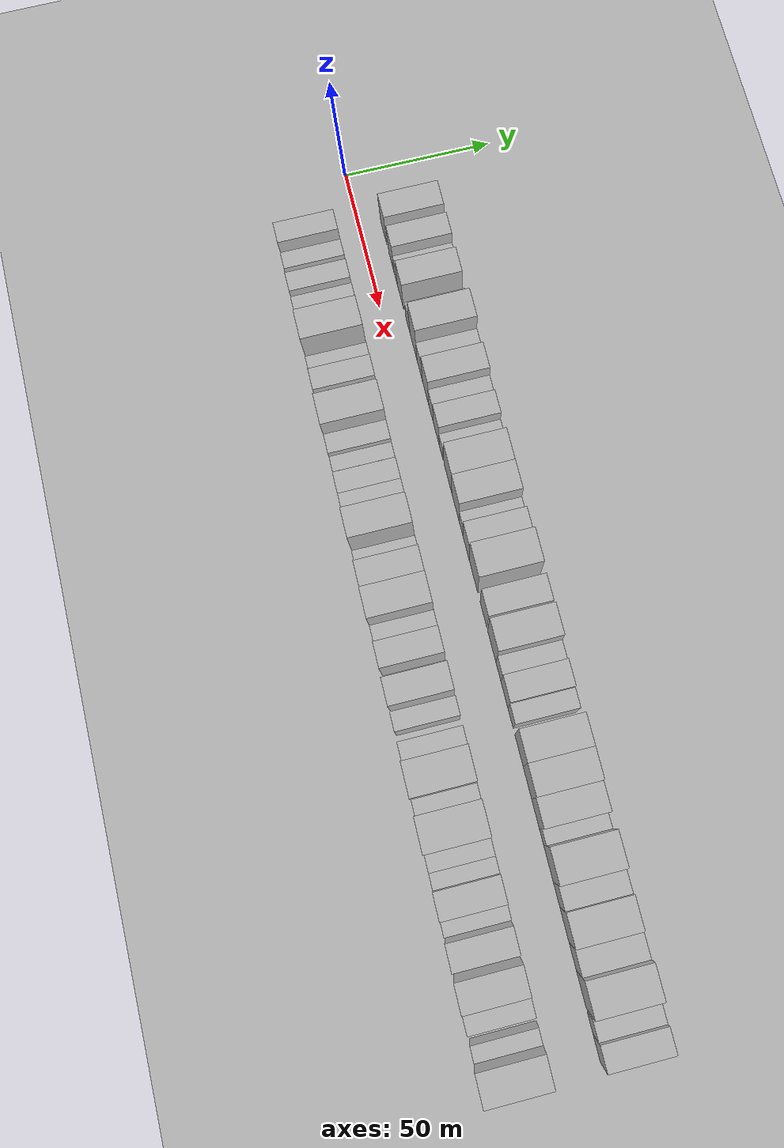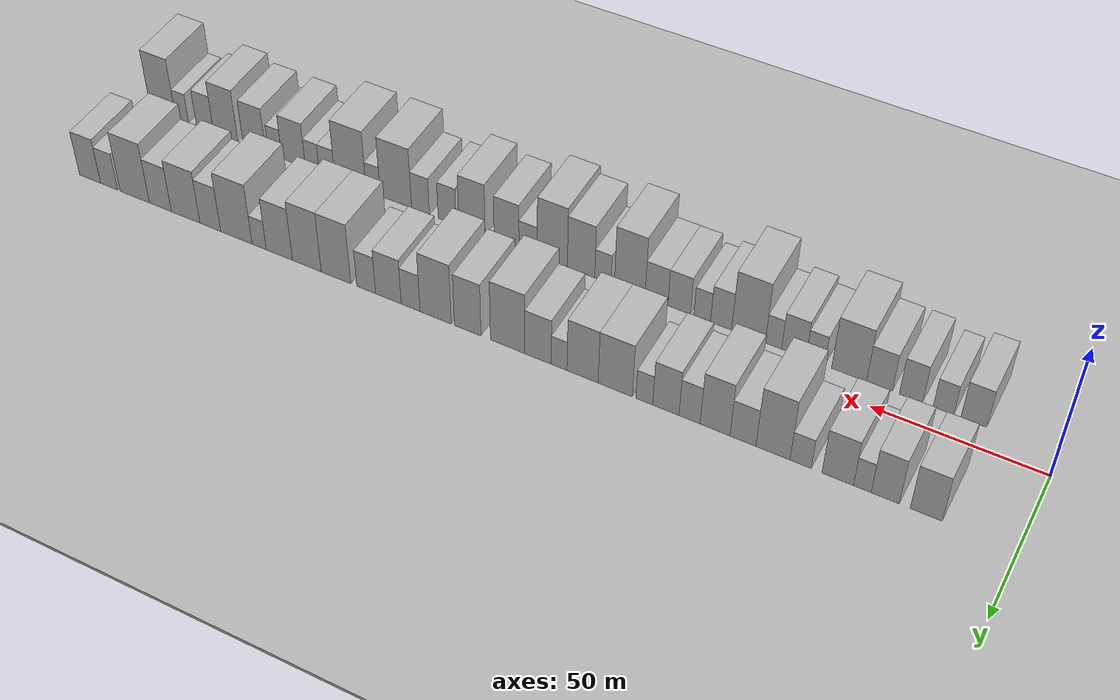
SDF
<?xml version="1.0" encoding="utf-8"?>

<sdf version="1.6">

   <world name="default">

      <gui fullscreen="0">

         <camera name="user_camera">

            <pose>-15 0 4.57585 0 0 0</pose>

            <view_controller>orbit</view_controller>

         </camera>

      </gui>

      <scene>

         <sky>

           <clouds>

             <speed>12</speed>

           </clouds>

         </sky>

         <ambient>0.4 0.4 0.4 1</ambient>

         <background>0.7 0.7 0.7 1</background>

         <shadows>1</shadows>

      </scene>

      <gravity>0 0 -9.8066</gravity>

      <magnetic_field>6e-06 2.3e-05 -4.2e-05</magnetic_field>

      <physics default="0" name="default_physics" type="ode">

         <ode>

            <solver>

               <type>quick</type>

               <iters>10</iters>

               <sor>1.0</sor>

               <use_dynamic_moi_rescaling>0</use_dynamic_moi_rescaling>

            </solver>

            <constraints>

               <cfm>0</cfm>

               <erp>0.2</erp>

               <contact_max_correcting_vel>100</contact_max_correcting_vel>

               <contact_surface_layer>0.001</contact_surface_layer>

            </constraints>

         </ode>

         <max_step_size>0.004</max_step_size>

         <real_time_factor>1</real_time_factor>

         <real_time_update_rate>250</real_time_update_rate>

      </physics>

      <light name="sun" type="directional">

         <cast_shadows>1</cast_shadows>

         <pose>0 0 10 0 0 0</pose>

         <diffuse>0.8 0.8 0.8 1</diffuse>

         <specular>0.2 0.2 0.2 1</specular>

         <attenuation>

            <range>1000</range>

            <constant>0.9</constant>

            <linear>0.01</linear>

            <quadratic>0.001</quadratic>

         </attenuation>

         <direction>-0.5 0.1 -0.9</direction>

      </light>

      <include>

         <name>ground_plane_1</name>

         <uri>model://HANNAS_ground_plane</uri>

         <pose>0 0 0  0 0 0</pose>

      </include>

      <include>

         <name>ground_plane_2</name>

         <uri>model://HANNAS_ground_plane</uri>

         <pose>100 0 0  0 0 0</pose>

      </include>

      <model name="building_1">

         <static>1</static>

         <pose frame="">24.3288 17.5000 0 0.000000 0.000000 1.570796</pose>

         <link name="link">

            <pose frame="">0 0 9.00 0 0 0</pose>

            <collision name="collision">

               <geometry>

                  <box>

                     <size>20.0000 8.6577 18.0000</size>

                  </box>

               </geometry>

               <max_contacts>10</max_contacts>

               <surface>

                  <contact>

                     <ode/>

                  </contact>

                  <bounce/>

                  <friction>

                     <torsional>

                        <ode/>

                     </torsional>

                     <ode/>

                  </friction>

               </surface>

            </collision>

            <visual name="visual">

               <cast_shadows>0</cast_shadows>

               <geometry>

                  <box>

                     <size>20.0000 8.6577 18.0000</size>

                  </box>

               </geometry>

               <material>

                  <script>

                     <uri>model://HANNAS_wall/materials/scripts</uri>

                     <uri>model://HANNAS_wall/materials/textures</uri>

                     <name>vrc/HANNAS_wall</name>

                  </script>

               </material>

            </visual>

            <self_collide>0</self_collide>

            <enable_wind>0</enable_wind>

            <kinematic>0</kinematic>

         </link>

      </model>

      <model name="building_2">

         <static>1</static>

         <pose frame="">35.4990 17.5000 0 0.000000 0.000000 1.570796</pose>

         <link name="link">

            <pose frame="">0 0 9.00 0 0 0</pose>

            <collision name="collision">

               <geometry>

                  <box>

                     <size>20.0000 7.6827 18.0000</size>

                  </box>

               </geometry>

               <max_contacts>10</max_contacts>

               <surface>

                  <contact>

                     <ode/>

                  </contact>

                  <bounce/>

                  <friction>

                     <torsional>

                        <ode/>

                     </torsional>

                     <ode/>

                  </friction>

               </surface>

            </collision>

            <visual name="visual">

               <cast_shadows>0</cast_shadows>

               <geometry>

                  <box>

                     <size>20.0000 7.6827 18.0000</size>

                  </box>

               </geometry>

               <material>

                  <script>

                     <uri>model://HANNAS_wall/materials/scripts</uri>

                     <uri>model://HANNAS_wall/materials/textures</uri>

                     <name>vrc/HANNAS_wall</name>

                  </script>

               </material>

            </visual>

            <self_collide>0</self_collide>

            <enable_wind>0</enable_wind>

            <kinematic>0</kinematic>

         </link>

      </model>

      <model name="building_3">

         <static>1</static>

         <pose frame="">41.7820 17.5000 0 0.000000 0.000000 1.570796</pose>

         <link name="link">

            <pose frame="">0 0 6.00 0 0 0</pose>

            <collision name="collision">

               <geometry>

                  <box>

                     <size>20.0000 4.8833 12.0000</size>

                  </box>

               </geometry>

               <max_contacts>10</max_contacts>

               <surface>

                  <contact>

                     <ode/>

                  </contact>

                  <bounce/>

                  <friction>

                     <torsional>

                        <ode/>

                     </torsional>

                     <ode/>

                  </friction>

               </surface>

            </collision>

            <visual name="visual">

               <cast_shadows>0</cast_shadows>

               <geometry>

                  <box>

                     <size>20.0000 4.8833 12.0000</size>

                  </box>

               </geometry>

               <material>

                  <script>

                     <uri>model://HANNAS_wall/materials/scripts</uri>

                     <uri>model://HANNAS_wall/materials/textures</uri>

                     <name>vrc/HANNAS_wall</name>

                  </script>

               </material>

            </visual>

            <self_collide>0</self_collide>

            <enable_wind>0</enable_wind>

            <kinematic>0</kinematic>

         </link>

      </model>

      <model name="building_4">

         <static>1</static>

         <pose frame="">48.6134 17.5000 0 0.000000 0.000000 1.570796</pose>

         <link name="link">

            <pose frame="">0 0 9.00 0 0 0</pose>

            <collision name="collision">

               <geometry>

                  <box>

                     <size>20.0000 8.7796 18.0000</size>

                  </box>

               </geometry>

               <max_contacts>10</max_contacts>

               <surface>

                  <contact>

                     <ode/>

                  </contact>

                  <bounce/>

                  <friction>

                     <torsional>

                        <ode/>

                     </torsional>

                     <ode/>

                  </friction>

               </surface>

            </collision>

            <visual name="visual">

               <cast_shadows>0</cast_shadows>

               <geometry>

                  <box>

                     <size>20.0000 8.7796 18.0000</size>

                  </box>

               </geometry>

               <material>

                  <script>

                     <uri>model://HANNAS_wall/materials/scripts</uri>

                     <uri>model://HANNAS_wall/materials/textures</uri>

                     <name>vrc/HANNAS_wall</name>

                  </script>

               </material>

            </visual>

            <self_collide>0</self_collide>

            <enable_wind>0</enable_wind>

            <kinematic>0</kinematic>

         </link>

      </model>

      <model name="building_5">

         <static>1</static>

         <pose frame="">59.0030 17.5000 0 0.000000 0.000000 1.570796</pose>

         <link name="link">

            <pose frame="">0 0 6.00 0 0 0</pose>

            <collision name="collision">

               <geometry>

                  <box>

                     <size>20.0000 5.9996 12.0000</size>

                  </box>

               </geometry>

               <max_contacts>10</max_contacts>

               <surface>

                  <contact>

                     <ode/>

                  </contact>

                  <bounce/>

                  <friction>

                     <torsional>

                        <ode/>

                     </torsional>

                     <ode/>

                  </friction>

               </surface>

            </collision>

            <visual name="visual">

               <cast_shadows>0</cast_shadows>

               <geometry>

                  <box>

                     <size>20.0000 5.9996 12.0000</size>

                  </box>

               </geometry>

               <material>

                  <script>

                     <uri>model://HANNAS_wall/materials/scripts</uri>

                     <uri>model://HANNAS_wall/materials/textures</uri>

                     <name>vrc/HANNAS_wall</name>

                  </script>

               </material>

            </visual>

            <self_collide>0</self_collide>

            <enable_wind>0</enable_wind>

            <kinematic>0</kinematic>

         </link>

      </model>

      <model name="building_6">

         <static>1</static>

         <pose frame="">66.8728 17.5000 0 0.000000 0.000000 1.570796</pose>

         <link name="link">

            <pose frame="">0 0 12.00 0 0 0</pose>

            <collision name="collision">

               <geometry>

                  <box>

                     <size>20.0000 9.7398 24.0000</size>

                  </box>

               </geometry>

               <max_contacts>10</max_contacts>

               <surface>

                  <contact>

                     <ode/>

                  </contact>

                  <bounce/>

                  <friction>

                     <torsional>

                        <ode/>

                     </torsional>

                     <ode/>

                  </friction>

               </surface>

            </collision>

            <visual name="visual">

               <cast_shadows>0</cast_shadows>

               <geometry>

                  <box>

                     <size>20.0000 9.7398 24.0000</size>

                  </box>

               </geometry>

               <material>

                  <script>

                     <uri>model://HANNAS_wall/materials/scripts</uri>

                     <uri>model://HANNAS_wall/materials/textures</uri>

                     <name>vrc/HANNAS_wall</name>

                  </script>

               </material>

            </visual>

            <self_collide>0</self_collide>

            <enable_wind>0</enable_wind>

            <kinematic>0</kinematic>

         </link>

      </model>

      <model name="building_7">

         <static>1</static>

         <pose frame="">75.4735 17.5000 0 0.000000 0.000000 1.570796</pose>

         <link name="link">

            <pose frame="">0 0 7.50 0 0 0</pose>

            <collision name="collision">

               <geometry>

                  <box>

                     <size>20.0000 7.4617 15.0000</size>

                  </box>

               </geometry>

               <max_contacts>10</max_contacts>

               <surface>

                  <contact>

                     <ode/>

                  </contact>

                  <bounce/>

                  <friction>

                     <torsional>

                        <ode/>

                     </torsional>

                     <ode/>

                  </friction>

               </surface>

            </collision>

            <visual name="visual">

               <cast_shadows>0</cast_shadows>

               <geometry>

                  <box>

                     <size>20.0000 7.4617 15.0000</size>

                  </box>

               </geometry>

               <material>

                  <script>

                     <uri>model://HANNAS_wall/materials/scripts</uri>

                     <uri>model://HANNAS_wall/materials/textures</uri>

                     <name>vrc/HANNAS_wall</name>

                  </script>

               </material>

            </visual>

            <self_collide>0</self_collide>

            <enable_wind>0</enable_wind>

            <kinematic>0</kinematic>

         </link>

      </model>

      <model name="building_8">

         <static>1</static>

         <pose frame="">83.5701 17.5000 0 0.000000 0.000000 1.570796</pose>

         <link name="link">

            <pose frame="">0 0 10.50 0 0 0</pose>

            <collision name="collision">

               <geometry>

                  <box>

                     <size>20.0000 8.7315 21.0000</size>

                  </box>

               </geometry>

               <max_contacts>10</max_contacts>

               <surface>

                  <contact>

                     <ode/>

                  </contact>

                  <bounce/>

                  <friction>

                     <torsional>

                        <ode/>

                     </torsional>

                     <ode/>

                  </friction>

               </surface>

            </collision>

            <visual name="visual">

               <cast_shadows>0</cast_shadows>

               <geometry>

                  <box>

                     <size>20.0000 8.7315 21.0000</size>

                  </box>

               </geometry>

               <material>

                  <script>

                     <uri>model://HANNAS_wall/materials/scripts</uri>

                     <uri>model://HANNAS_wall/materials/textures</uri>

                     <name>vrc/HANNAS_wall</name>

                  </script>

               </material>

            </visual>

            <self_collide>0</self_collide>

            <enable_wind>0</enable_wind>

            <kinematic>0</kinematic>

         </link>

      </model>

      <model name="building_9">

         <static>1</static>

         <pose frame="">91.0407 17.5000 0 0.000000 0.000000 1.570796</pose>

         <link name="link">

            <pose frame="">0 0 7.50 0 0 0</pose>

            <collision name="collision">

               <geometry>

                  <box>

                     <size>20.0000 6.2097 15.0000</size>

                  </box>

               </geometry>

               <max_contacts>10</max_contacts>

               <surface>

                  <contact>

                     <ode/>

                  </contact>

                  <bounce/>

                  <friction>

                     <torsional>

                        <ode/>

                     </torsional>

                     <ode/>

                  </friction>

               </surface>

            </collision>

            <visual name="visual">

               <cast_shadows>0</cast_shadows>

               <geometry>

                  <box>

                     <size>20.0000 6.2097 15.0000</size>

                  </box>

               </geometry>

               <material>

                  <script>

                     <uri>model://HANNAS_wall/materials/scripts</uri>

                     <uri>model://HANNAS_wall/materials/textures</uri>

                     <name>vrc/HANNAS_wall</name>

                  </script>

               </material>

            </visual>

            <self_collide>0</self_collide>

            <enable_wind>0</enable_wind>

            <kinematic>0</kinematic>

         </link>

      </model>

      <model name="building_10">

         <static>1</static>

         <pose frame="">98.0474 17.5000 0 0.000000 0.000000 1.570796</pose>

         <link name="link">

            <pose frame="">0 0 9.00 0 0 0</pose>

            <collision name="collision">

               <geometry>

                  <box>

                     <size>20.0000 7.8037 18.0000</size>

                  </box>

               </geometry>

               <max_contacts>10</max_contacts>

               <surface>

                  <contact>

                     <ode/>

                  </contact>

                  <bounce/>

                  <friction>

                     <torsional>

                        <ode/>

                     </torsional>

                     <ode/>

                  </friction>

               </surface>

            </collision>

            <visual name="visual">

               <cast_shadows>0</cast_shadows>

               <geometry>

                  <box>

                     <size>20.0000 7.8037 18.0000</size>

                  </box>

               </geometry>

               <material>

                  <script>

                     <uri>model://HANNAS_wall/materials/scripts</uri>

                     <uri>model://HANNAS_wall/materials/textures</uri>

                     <name>vrc/HANNAS_wall</name>

                  </script>

               </material>

            </visual>

            <self_collide>0</self_collide>

            <enable_wind>0</enable_wind>

            <kinematic>0</kinematic>

         </link>

      </model>

      <model name="building_11">

         <static>1</static>

         <pose frame="">104.4831 17.5000 0 0.000000 0.000000 1.570796</pose>

         <link name="link">

            <pose frame="">0 0 6.00 0 0 0</pose>

            <collision name="collision">

               <geometry>

                  <box>

                     <size>20.0000 5.0678 12.0000</size>

                  </box>

               </geometry>

               <max_contacts>10</max_contacts>

               <surface>

                  <contact>

                     <ode/>

                  </contact>

                  <bounce/>

                  <friction>

                     <torsional>

                        <ode/>

                     </torsional>

                     <ode/>

                  </friction>

               </surface>

            </collision>

            <visual name="visual">

               <cast_shadows>0</cast_shadows>

               <geometry>

                  <box>

                     <size>20.0000 5.0678 12.0000</size>

                  </box>

               </geometry>

               <material>

                  <script>

                     <uri>model://HANNAS_wall/materials/scripts</uri>

                     <uri>model://HANNAS_wall/materials/textures</uri>

                     <name>vrc/HANNAS_wall</name>

                  </script>

               </material>

            </visual>

            <self_collide>0</self_collide>

            <enable_wind>0</enable_wind>

            <kinematic>0</kinematic>

         </link>

      </model>

      <model name="building_12">

         <static>1</static>

         <pose frame="">113.2187 17.5000 0 0.000000 0.000000 1.570796</pose>

         <link name="link">

            <pose frame="">0 0 10.50 0 0 0</pose>

            <collision name="collision">

               <geometry>

                  <box>

                     <size>20.0000 10.4034 21.0000</size>

                  </box>

               </geometry>

               <max_contacts>10</max_contacts>

               <surface>

                  <contact>

                     <ode/>

                  </contact>

                  <bounce/>

                  <friction>

                     <torsional>

                        <ode/>

                     </torsional>

                     <ode/>

                  </friction>

               </surface>

            </collision>

            <visual name="visual">

               <cast_shadows>0</cast_shadows>

               <geometry>

                  <box>

                     <size>20.0000 10.4034 21.0000</size>

                  </box>

               </geometry>

               <material>

                  <script>

                     <uri>model://HANNAS_wall/materials/scripts</uri>

                     <uri>model://HANNAS_wall/materials/textures</uri>

                     <name>vrc/HANNAS_wall</name>

                  </script>

               </material>

            </visual>

            <self_collide>0</self_collide>

            <enable_wind>0</enable_wind>

            <kinematic>0</kinematic>

         </link>

      </model>

      <model name="building_13">

         <static>1</static>

         <pose frame="">123.2028 17.5000 0 0.000000 0.000000 1.570796</pose>

         <link name="link">

            <pose frame="">0 0 10.50 0 0 0</pose>

            <collision name="collision">

               <geometry>

                  <box>

                     <size>20.0000 9.5647 21.0000</size>

                  </box>

               </geometry>

               <max_contacts>10</max_contacts>

               <surface>

                  <contact>

                     <ode/>

                  </contact>

                  <bounce/>

                  <friction>

                     <torsional>

                        <ode/>

                     </torsional>

                     <ode/>

                  </friction>

               </surface>

            </collision>

            <visual name="visual">

               <cast_shadows>0</cast_shadows>

               <geometry>

                  <box>

                     <size>20.0000 9.5647 21.0000</size>

                  </box>

               </geometry>

               <material>

                  <script>

                     <uri>model://HANNAS_wall/materials/scripts</uri>

                     <uri>model://HANNAS_wall/materials/textures</uri>

                     <name>vrc/HANNAS_wall</name>

                  </script>

               </material>

            </visual>

            <self_collide>0</self_collide>

            <enable_wind>0</enable_wind>

            <kinematic>0</kinematic>

         </link>

      </model>

      <model name="building_14">

         <static>1</static>

         <pose frame="">130.4264 17.5000 0 0.000000 0.000000 1.570796</pose>

         <link name="link">

            <pose frame="">0 0 6.00 0 0 0</pose>

            <collision name="collision">

               <geometry>

                  <box>

                     <size>20.0000 4.8826 12.0000</size>

                  </box>

               </geometry>

               <max_contacts>10</max_contacts>

               <surface>

                  <contact>

                     <ode/>

                  </contact>

                  <bounce/>

                  <friction>

                     <torsional>

                        <ode/>

                     </torsional>

                     <ode/>

                  </friction>

               </surface>

            </collision>

            <visual name="visual">

               <cast_shadows>0</cast_shadows>

               <geometry>

                  <box>

                     <size>20.0000 4.8826 12.0000</size>

                  </box>

               </geometry>

               <material>

                  <script>

                     <uri>model://HANNAS_wall/materials/scripts</uri>

                     <uri>model://HANNAS_wall/materials/textures</uri>

                     <name>vrc/HANNAS_wall</name>

                  </script>

               </material>

            </visual>

            <self_collide>0</self_collide>

            <enable_wind>0</enable_wind>

            <kinematic>0</kinematic>

         </link>

      </model>

      <model name="building_15">

         <static>1</static>

         <pose frame="">136.9708 17.5000 0 0.000000 0.000000 1.570796</pose>

         <link name="link">

            <pose frame="">0 0 9.00 0 0 0</pose>

            <collision name="collision">

               <geometry>

                  <box>

                     <size>20.0000 8.2061 18.0000</size>

                  </box>

               </geometry>

               <max_contacts>10</max_contacts>

               <surface>

                  <contact>

                     <ode/>

                  </contact>

                  <bounce/>

                  <friction>

                     <torsional>

                        <ode/>

                     </torsional>

                     <ode/>

                  </friction>

               </surface>

            </collision>

            <visual name="visual">

               <cast_shadows>0</cast_shadows>

               <geometry>

                  <box>

                     <size>20.0000 8.2061 18.0000</size>

                  </box>

               </geometry>

               <material>

                  <script>

                     <uri>model://HANNAS_wall/materials/scripts</uri>

                     <uri>model://HANNAS_wall/materials/textures</uri>

                     <name>vrc/HANNAS_wall</name>

                  </script>

               </material>

            </visual>

            <self_collide>0</self_collide>

            <enable_wind>0</enable_wind>

            <kinematic>0</kinematic>

         </link>

      </model>

      <model name="building_16">

         <static>1</static>

         <pose frame="">146.4967 17.5000 0 0.000000 0.000000 1.570796</pose>

         <link name="link">

            <pose frame="">0 0 12.00 0 0 0</pose>

            <collision name="collision">

               <geometry>

                  <box>

                     <size>20.0000 10.8458 24.0000</size>

                  </box>

               </geometry>

               <max_contacts>10</max_contacts>

               <surface>

                  <contact>

                     <ode/>

                  </contact>

                  <bounce/>

                  <friction>

                     <torsional>

                        <ode/>

                     </torsional>

                     <ode/>

                  </friction>

               </surface>

            </collision>

            <visual name="visual">

               <cast_shadows>0</cast_shadows>

               <geometry>

                  <box>

                     <size>20.0000 10.8458 24.0000</size>

                  </box>

               </geometry>

               <material>

                  <script>

                     <uri>model://HANNAS_wall/materials/scripts</uri>

                     <uri>model://HANNAS_wall/materials/textures</uri>

                     <name>vrc/HANNAS_wall</name>

                  </script>

               </material>

            </visual>

            <self_collide>0</self_collide>

            <enable_wind>0</enable_wind>

            <kinematic>0</kinematic>

         </link>

      </model>

      <model name="building_17">

         <static>1</static>

         <pose frame="">159.1878 17.5000 0 0.000000 0.000000 1.570796</pose>

         <link name="link">

            <pose frame="">0 0 10.50 0 0 0</pose>

            <collision name="collision">

               <geometry>

                  <box>

                     <size>20.0000 8.5364 21.0000</size>

                  </box>

               </geometry>

               <max_contacts>10</max_contacts>

               <surface>

                  <contact>

                     <ode/>

                  </contact>

                  <bounce/>

                  <friction>

                     <torsional>

                        <ode/>

                     </torsional>

                     <ode/>

                  </friction>

               </surface>

            </collision>

            <visual name="visual">

               <cast_shadows>0</cast_shadows>

               <geometry>

                  <box>

                     <size>20.0000 8.5364 21.0000</size>

                  </box>

               </geometry>

               <material>

                  <script>

                     <uri>model://HANNAS_wall/materials/scripts</uri>

                     <uri>model://HANNAS_wall/materials/textures</uri>

                     <name>vrc/HANNAS_wall</name>

                  </script>

               </material>

            </visual>

            <self_collide>0</self_collide>

            <enable_wind>0</enable_wind>

            <kinematic>0</kinematic>

         </link>

      </model>

      <model name="building_18">

         <static>1</static>

         <pose frame="">169.5330 17.5000 0 0.000000 0.000000 1.570796</pose>

         <link name="link">

            <pose frame="">0 0 12.00 0 0 0</pose>

            <collision name="collision">

               <geometry>

                  <box>

                     <size>20.0000 10.1541 24.0000</size>

                  </box>

               </geometry>

               <max_contacts>10</max_contacts>

               <surface>

                  <contact>

                     <ode/>

                  </contact>

                  <bounce/>

                  <friction>

                     <torsional>

                        <ode/>

                     </torsional>

                     <ode/>

                  </friction>

               </surface>

            </collision>

            <visual name="visual">

               <cast_shadows>0</cast_shadows>

               <geometry>

                  <box>

                     <size>20.0000 10.1541 24.0000</size>

                  </box>

               </geometry>

               <material>

                  <script>

                     <uri>model://HANNAS_wall/materials/scripts</uri>

                     <uri>model://HANNAS_wall/materials/textures</uri>

                     <name>vrc/HANNAS_wall</name>

                  </script>

               </material>

            </visual>

            <self_collide>0</self_collide>

            <enable_wind>0</enable_wind>

            <kinematic>0</kinematic>

         </link>

      </model>

      <model name="building_19">

         <static>1</static>

         <pose frame="">177.7087 17.5000 0 0.000000 0.000000 1.570796</pose>

         <link name="link">

            <pose frame="">0 0 7.50 0 0 0</pose>

            <collision name="collision">

               <geometry>

                  <box>

                     <size>20.0000 6.1973 15.0000</size>

                  </box>

               </geometry>

               <max_contacts>10</max_contacts>

               <surface>

                  <contact>

                     <ode/>

                  </contact>

                  <bounce/>

                  <friction>

                     <torsional>

                        <ode/>

                     </torsional>

                     <ode/>

                  </friction>

               </surface>

            </collision>

            <visual name="visual">

               <cast_shadows>0</cast_shadows>

               <geometry>

                  <box>

                     <size>20.0000 6.1973 15.0000</size>

                  </box>

               </geometry>

               <material>

                  <script>

                     <uri>model://HANNAS_wall/materials/scripts</uri>

                     <uri>model://HANNAS_wall/materials/textures</uri>

                     <name>vrc/HANNAS_wall</name>

                  </script>

               </material>

            </visual>

            <self_collide>0</self_collide>

            <enable_wind>0</enable_wind>

            <kinematic>0</kinematic>

         </link>

      </model>

      <model name="building_20">

         <static>1</static>

         <pose frame="">185.0354 17.5000 0 0.000000 0.000000 1.570796</pose>

         <link name="link">

            <pose frame="">0 0 9.00 0 0 0</pose>

            <collision name="collision">

               <geometry>

                  <box>

                     <size>20.0000 8.4561 18.0000</size>

                  </box>

               </geometry>

               <max_contacts>10</max_contacts>

               <surface>

                  <contact>

                     <ode/>

                  </contact>

                  <bounce/>

                  <friction>

                     <torsional>

                        <ode/>

                     </torsional>

                     <ode/>

                  </friction>

               </surface>

            </collision>

            <visual name="visual">

               <cast_shadows>0</cast_shadows>

               <geometry>

                  <box>

                     <size>20.0000 8.4561 18.0000</size>

                  </box>

               </geometry>

               <material>

                  <script>

                     <uri>model://HANNAS_wall/materials/scripts</uri>

                     <uri>model://HANNAS_wall/materials/textures</uri>

                     <name>vrc/HANNAS_wall</name>

                  </script>

               </material>

            </visual>

            <self_collide>0</self_collide>

            <enable_wind>0</enable_wind>

            <kinematic>0</kinematic>

         </link>

      </model>

      <model name="building_21">

         <static>1</static>

         <pose frame="">192.4085 17.5000 0 0.000000 0.000000 1.570796</pose>

         <link name="link">

            <pose frame="">0 0 7.50 0 0 0</pose>

            <collision name="collision">

               <geometry>

                  <box>

                     <size>20.0000 6.2901 15.0000</size>

                  </box>

               </geometry>

               <max_contacts>10</max_contacts>

               <surface>

                  <contact>

                     <ode/>

                  </contact>

                  <bounce/>

                  <friction>

                     <torsional>

                        <ode/>

                     </torsional>

                     <ode/>

                  </friction>

               </surface>

            </collision>

            <visual name="visual">

               <cast_shadows>0</cast_shadows>

               <geometry>

                  <box>

                     <size>20.0000 6.2901 15.0000</size>

                  </box>

               </geometry>

               <material>

                  <script>

                     <uri>model://HANNAS_wall/materials/scripts</uri>

                     <uri>model://HANNAS_wall/materials/textures</uri>

                     <name>vrc/HANNAS_wall</name>

                  </script>

               </material>

            </visual>

            <self_collide>0</self_collide>

            <enable_wind>0</enable_wind>

            <kinematic>0</kinematic>

         </link>

      </model>

      <model name="building_22">

         <static>1</static>

         <pose frame="">202.5575 17.5000 0 0.000000 0.000000 1.570796</pose>

         <link name="link">

            <pose frame="">0 0 12.00 0 0 0</pose>

            <collision name="collision">

               <geometry>

                  <box>

                     <size>20.0000 10.0080 24.0000</size>

                  </box>

               </geometry>

               <max_contacts>10</max_contacts>

               <surface>

                  <contact>

                     <ode/>

                  </contact>

                  <bounce/>

                  <friction>

                     <torsional>

                        <ode/>

                     </torsional>

                     <ode/>

                  </friction>

               </surface>

            </collision>

            <visual name="visual">

               <cast_shadows>0</cast_shadows>

               <geometry>

                  <box>

                     <size>20.0000 10.0080 24.0000</size>

                  </box>

               </geometry>

               <material>

                  <script>

                     <uri>model://HANNAS_wall/materials/scripts</uri>

                     <uri>model://HANNAS_wall/materials/textures</uri>

                     <name>vrc/HANNAS_wall</name>

                  </script>

               </material>

            </visual>

            <self_collide>0</self_collide>

            <enable_wind>0</enable_wind>

            <kinematic>0</kinematic>

         </link>

      </model>

      <model name="building_23">

         <static>1</static>

         <pose frame="">212.4708 17.5000 0 0.000000 0.000000 1.570796</pose>

         <link name="link">

            <pose frame="">0 0 12.00 0 0 0</pose>

            <collision name="collision">

               <geometry>

                  <box>

                     <size>20.0000 9.8185 24.0000</size>

                  </box>

               </geometry>

               <max_contacts>10</max_contacts>

               <surface>

                  <contact>

                     <ode/>

                  </contact>

                  <bounce/>

                  <friction>

                     <torsional>

                        <ode/>

                     </torsional>

                     <ode/>

                  </friction>

               </surface>

            </collision>

            <visual name="visual">

               <cast_shadows>0</cast_shadows>

               <geometry>

                  <box>

                     <size>20.0000 9.8185 24.0000</size>

                  </box>

               </geometry>

               <material>

                  <script>

                     <uri>model://HANNAS_wall/materials/scripts</uri>

                     <uri>model://HANNAS_wall/materials/textures</uri>

                     <name>vrc/HANNAS_wall</name>

                  </script>

               </material>

            </visual>

            <self_collide>0</self_collide>

            <enable_wind>0</enable_wind>

            <kinematic>0</kinematic>

         </link>

      </model>

      <model name="building_24">

         <static>1</static>

         <pose frame="">221.9110 17.5000 0 0.000000 0.000000 1.570796</pose>

         <link name="link">

            <pose frame="">0 0 10.50 0 0 0</pose>

            <collision name="collision">

               <geometry>

                  <box>

                     <size>20.0000 9.0620 21.0000</size>

                  </box>

               </geometry>

               <max_contacts>10</max_contacts>

               <surface>

                  <contact>

                     <ode/>

                  </contact>

                  <bounce/>

                  <friction>

                     <torsional>

                        <ode/>

                     </torsional>

                     <ode/>

                  </friction>

               </surface>

            </collision>

            <visual name="visual">

               <cast_shadows>0</cast_shadows>

               <geometry>

                  <box>

                     <size>20.0000 9.0620 21.0000</size>

                  </box>

               </geometry>

               <material>

                  <script>

                     <uri>model://HANNAS_wall/materials/scripts</uri>

                     <uri>model://HANNAS_wall/materials/textures</uri>

                     <name>vrc/HANNAS_wall</name>

                  </script>

               </material>

            </visual>

            <self_collide>0</self_collide>

            <enable_wind>0</enable_wind>

            <kinematic>0</kinematic>

         </link>

      </model>

      <model name="building_25">

         <static>1</static>

         <pose frame="">228.9191 17.5000 0 0.000000 0.000000 1.570796</pose>

         <link name="link">

            <pose frame="">0 0 6.00 0 0 0</pose>

            <collision name="collision">

               <geometry>

                  <box>

                     <size>20.0000 4.9543 12.0000</size>

                  </box>

               </geometry>

               <max_contacts>10</max_contacts>

               <surface>

                  <contact>

                     <ode/>

                  </contact>

                  <bounce/>

                  <friction>

                     <torsional>

                        <ode/>

                     </torsional>

                     <ode/>

                  </friction>

               </surface>

            </collision>

            <visual name="visual">

               <cast_shadows>0</cast_shadows>

               <geometry>

                  <box>

                     <size>20.0000 4.9543 12.0000</size>

                  </box>

               </geometry>

               <material>

                  <script>

                     <uri>model://HANNAS_wall/materials/scripts</uri>

                     <uri>model://HANNAS_wall/materials/textures</uri>

                     <name>vrc/HANNAS_wall</name>

                  </script>

               </material>

            </visual>

            <self_collide>0</self_collide>

            <enable_wind>0</enable_wind>

            <kinematic>0</kinematic>

         </link>

      </model>

      <model name="building_26">

         <static>1</static>

         <pose frame="">236.9182 17.5000 0 0.000000 0.000000 1.570796</pose>

         <link name="link">

            <pose frame="">0 0 12.00 0 0 0</pose>

            <collision name="collision">

               <geometry>

                  <box>

                     <size>20.0000 11.0440 24.0000</size>

                  </box>

               </geometry>

               <max_contacts>10</max_contacts>

               <surface>

                  <contact>

                     <ode/>

                  </contact>

                  <bounce/>

                  <friction>

                     <torsional>

                        <ode/>

                     </torsional>

                     <ode/>

                  </friction>

               </surface>

            </collision>

            <visual name="visual">

               <cast_shadows>0</cast_shadows>

               <geometry>

                  <box>

                     <size>20.0000 11.0440 24.0000</size>

                  </box>

               </geometry>

               <material>

                  <script>

                     <uri>model://HANNAS_wall/materials/scripts</uri>

                     <uri>model://HANNAS_wall/materials/textures</uri>

                     <name>vrc/HANNAS_wall</name>

                  </script>

               </material>

            </visual>

            <self_collide>0</self_collide>

            <enable_wind>0</enable_wind>

            <kinematic>0</kinematic>

         </link>

      </model>

      <model name="building_27">

         <static>1</static>

         <pose frame="">246.1286 17.5000 0 0.000000 0.000000 1.570796</pose>

         <link name="link">

            <pose frame="">0 0 9.00 0 0 0</pose>

            <collision name="collision">

               <geometry>

                  <box>

                     <size>20.0000 7.3767 18.0000</size>

                  </box>

               </geometry>

               <max_contacts>10</max_contacts>

               <surface>

                  <contact>

                     <ode/>

                  </contact>

                  <bounce/>

                  <friction>

                     <torsional>

                        <ode/>

                     </torsional>

                     <ode/>

                  </friction>

               </surface>

            </collision>

            <visual name="visual">

               <cast_shadows>0</cast_shadows>

               <geometry>

                  <box>

                     <size>20.0000 7.3767 18.0000</size>

                  </box>

               </geometry>

               <material>

                  <script>

                     <uri>model://HANNAS_wall/materials/scripts</uri>

                     <uri>model://HANNAS_wall/materials/textures</uri>

                     <name>vrc/HANNAS_wall</name>

                  </script>

               </material>

            </visual>

            <self_collide>0</self_collide>

            <enable_wind>0</enable_wind>

            <kinematic>0</kinematic>

         </link>

      </model>

      <model name="building_28">

         <static>1</static>

         <pose frame="">254.9602 17.5000 0 0.000000 0.000000 1.570796</pose>

         <link name="link">

            <pose frame="">0 0 10.50 0 0 0</pose>

            <collision name="collision">

               <geometry>

                  <box>

                     <size>20.0000 10.2866 21.0000</size>

                  </box>

               </geometry>

               <max_contacts>10</max_contacts>

               <surface>

                  <contact>

                     <ode/>

                  </contact>

                  <bounce/>

                  <friction>

                     <torsional>

                        <ode/>

                     </torsional>

                     <ode/>

                  </friction>

               </surface>

            </collision>

            <visual name="visual">

               <cast_shadows>0</cast_shadows>

               <geometry>

                  <box>

                     <size>20.0000 10.2866 21.0000</size>

                  </box>

               </geometry>

               <material>

                  <script>

                     <uri>model://HANNAS_wall/materials/scripts</uri>

                     <uri>model://HANNAS_wall/materials/textures</uri>

                     <name>vrc/HANNAS_wall</name>

                  </script>

               </material>

            </visual>

            <self_collide>0</self_collide>

            <enable_wind>0</enable_wind>

            <kinematic>0</kinematic>

         </link>

      </model>

      <model name="building_29">

         <static>1</static>

         <pose frame="">264.1082 17.5000 0 0.000000 0.000000 1.570796</pose>

         <link name="link">

            <pose frame="">0 0 9.00 0 0 0</pose>

            <collision name="collision">

               <geometry>

                  <box>

                     <size>20.0000 8.0094 18.0000</size>

                  </box>

               </geometry>

               <max_contacts>10</max_contacts>

               <surface>

                  <contact>

                     <ode/>

                  </contact>

                  <bounce/>

                  <friction>

                     <torsional>

                        <ode/>

                     </torsional>

                     <ode/>

                  </friction>

               </surface>

            </collision>

            <visual name="visual">

               <cast_shadows>0</cast_shadows>

               <geometry>

                  <box>

                     <size>20.0000 8.0094 18.0000</size>

                  </box>

               </geometry>

               <material>

                  <script>

                     <uri>model://HANNAS_wall/materials/scripts</uri>

                     <uri>model://HANNAS_wall/materials/textures</uri>

                     <name>vrc/HANNAS_wall</name>

                  </script>

               </material>

            </visual>

            <self_collide>0</self_collide>

            <enable_wind>0</enable_wind>

            <kinematic>0</kinematic>

         </link>

      </model>

      <model name="building_30">

         <static>1</static>

         <pose frame="">273.4680 17.5000 0 0.000000 0.000000 1.570796</pose>

         <link name="link">

            <pose frame="">0 0 12.00 0 0 0</pose>

            <collision name="collision">

               <geometry>

                  <box>

                     <size>20.0000 10.7102 24.0000</size>

                  </box>

               </geometry>

               <max_contacts>10</max_contacts>

               <surface>

                  <contact>

                     <ode/>

                  </contact>

                  <bounce/>

                  <friction>

                     <torsional>

                        <ode/>

                     </torsional>

                     <ode/>

                  </friction>

               </surface>

            </collision>

            <visual name="visual">

               <cast_shadows>0</cast_shadows>

               <geometry>

                  <box>

                     <size>20.0000 10.7102 24.0000</size>

                  </box>

               </geometry>

               <material>

                  <script>

                     <uri>model://HANNAS_wall/materials/scripts</uri>

                     <uri>model://HANNAS_wall/materials/textures</uri>

                     <name>vrc/HANNAS_wall</name>

                  </script>

               </material>

            </visual>

            <self_collide>0</self_collide>

            <enable_wind>0</enable_wind>

            <kinematic>0</kinematic>

         </link>

      </model>

      <model name="building_31">

         <static>1</static>

         <pose frame="">282.9808 17.5000 0 0.000000 0.000000 1.570796</pose>

         <link name="link">

            <pose frame="">0 0 7.50 0 0 0</pose>

            <collision name="collision">

               <geometry>

                  <box>

                     <size>20.0000 6.3152 15.0000</size>

                  </box>

               </geometry>

               <max_contacts>10</max_contacts>

               <surface>

                  <contact>

                     <ode/>

                  </contact>

                  <bounce/>

                  <friction>

                     <torsional>

                        <ode/>

                     </torsional>

                     <ode/>

                  </friction>

               </surface>

            </collision>

            <visual name="visual">

               <cast_shadows>0</cast_shadows>

               <geometry>

                  <box>

                     <size>20.0000 6.3152 15.0000</size>

                  </box>

               </geometry>

               <material>

                  <script>

                     <uri>model://HANNAS_wall/materials/scripts</uri>

                     <uri>model://HANNAS_wall/materials/textures</uri>

                     <name>vrc/HANNAS_wall</name>

                  </script>

               </material>

            </visual>

            <self_collide>0</self_collide>

            <enable_wind>0</enable_wind>

            <kinematic>0</kinematic>

         </link>

      </model>

      <model name="building_32">

         <static>1</static>

         <pose frame="">290.0704 17.5000 0 0.000000 0.000000 1.570796</pose>

         <link name="link">

            <pose frame="">0 0 9.00 0 0 0</pose>

            <collision name="collision">

               <geometry>

                  <box>

                     <size>20.0000 7.8642 18.0000</size>

                  </box>

               </geometry>

               <max_contacts>10</max_contacts>

               <surface>

                  <contact>

                     <ode/>

                  </contact>

                  <bounce/>

                  <friction>

                     <torsional>

                        <ode/>

                     </torsional>

                     <ode/>

                  </friction>

               </surface>

            </collision>

            <visual name="visual">

               <cast_shadows>0</cast_shadows>

               <geometry>

                  <box>

                     <size>20.0000 7.8642 18.0000</size>

                  </box>

               </geometry>

               <material>

                  <script>

                     <uri>model://HANNAS_wall/materials/scripts</uri>

                     <uri>model://HANNAS_wall/materials/textures</uri>

                     <name>vrc/HANNAS_wall</name>

                  </script>

               </material>

            </visual>

            <self_collide>0</self_collide>

            <enable_wind>0</enable_wind>

            <kinematic>0</kinematic>

         </link>

      </model>

      <model name="building_33">

         <static>1</static>

         <pose frame="">23.6141 -17.5000 0 0.000000 0.000000 1.570796</pose>

         <link name="link">

            <pose frame="">0 0 7.50 0 0 0</pose>

            <collision name="collision">

               <geometry>

                  <box>

                     <size>20.0000 7.2282 15.0000</size>

                  </box>

               </geometry>

               <max_contacts>10</max_contacts>

               <surface>

                  <contact>

                     <ode/>

                  </contact>

                  <bounce/>

                  <friction>

                     <torsional>

                        <ode/>

                     </torsional>

                     <ode/>

                  </friction>

               </surface>

            </collision>

            <visual name="visual">

               <cast_shadows>0</cast_shadows>

               <geometry>

                  <box>

                     <size>20.0000 7.2282 15.0000</size>

                  </box>

               </geometry>

               <material>

                  <script>

                     <uri>model://HANNAS_wall/materials/scripts</uri>

                     <uri>model://HANNAS_wall/materials/textures</uri>

                     <name>vrc/HANNAS_wall</name>

                  </script>

               </material>

            </visual>

            <self_collide>0</self_collide>

            <enable_wind>0</enable_wind>

            <kinematic>0</kinematic>

         </link>

      </model>

      <model name="building_34">

         <static>1</static>

         <pose frame="">32.1389 -17.5000 0 0.000000 0.000000 1.570796</pose>

         <link name="link">

            <pose frame="">0 0 6.00 0 0 0</pose>

            <collision name="collision">

               <geometry>

                  <box>

                     <size>20.0000 5.8214 12.0000</size>

                  </box>

               </geometry>

               <max_contacts>10</max_contacts>

               <surface>

                  <contact>

                     <ode/>

                  </contact>

                  <bounce/>

                  <friction>

                     <torsional>

                        <ode/>

                     </torsional>

                     <ode/>

                  </friction>

               </surface>

            </collision>

            <visual name="visual">

               <cast_shadows>0</cast_shadows>

               <geometry>

                  <box>

                     <size>20.0000 5.8214 12.0000</size>

                  </box>

               </geometry>

               <material>

                  <script>

                     <uri>model://HANNAS_wall/materials/scripts</uri>

                     <uri>model://HANNAS_wall/materials/textures</uri>

                     <name>vrc/HANNAS_wall</name>

                  </script>

               </material>

            </visual>

            <self_collide>0</self_collide>

            <enable_wind>0</enable_wind>

            <kinematic>0</kinematic>

         </link>

      </model>

      <model name="building_35">

         <static>1</static>

         <pose frame="">41.3731 -17.5000 0 0.000000 0.000000 1.570796</pose>

         <link name="link">

            <pose frame="">0 0 7.50 0 0 0</pose>

            <collision name="collision">

               <geometry>

                  <box>

                     <size>20.0000 6.6470 15.0000</size>

                  </box>

               </geometry>

               <max_contacts>10</max_contacts>

               <surface>

                  <contact>

                     <ode/>

                  </contact>

                  <bounce/>

                  <friction>

                     <torsional>

                        <ode/>

                     </torsional>

                     <ode/>

                  </friction>

               </surface>

            </collision>

            <visual name="visual">

               <cast_shadows>0</cast_shadows>

               <geometry>

                  <box>

                     <size>20.0000 6.6470 15.0000</size>

                  </box>

               </geometry>

               <material>

                  <script>

                     <uri>model://HANNAS_wall/materials/scripts</uri>

                     <uri>model://HANNAS_wall/materials/textures</uri>

                     <name>vrc/HANNAS_wall</name>

                  </script>

               </material>

            </visual>

            <self_collide>0</self_collide>

            <enable_wind>0</enable_wind>

            <kinematic>0</kinematic>

         </link>

      </model>

      <model name="building_36">

         <static>1</static>

         <pose frame="">50.4240 -17.5000 0 0.000000 0.000000 1.570796</pose>

         <link name="link">

            <pose frame="">0 0 7.50 0 0 0</pose>

            <collision name="collision">

               <geometry>

                  <box>

                     <size>20.0000 7.4547 15.0000</size>

                  </box>

               </geometry>

               <max_contacts>10</max_contacts>

               <surface>

                  <contact>

                     <ode/>

                  </contact>

                  <bounce/>

                  <friction>

                     <torsional>

                        <ode/>

                     </torsional>

                     <ode/>

                  </friction>

               </surface>

            </collision>

            <visual name="visual">

               <cast_shadows>0</cast_shadows>

               <geometry>

                  <box>

                     <size>20.0000 7.4547 15.0000</size>

                  </box>

               </geometry>

               <material>

                  <script>

                     <uri>model://HANNAS_wall/materials/scripts</uri>

                     <uri>model://HANNAS_wall/materials/textures</uri>

                     <name>vrc/HANNAS_wall</name>

                  </script>

               </material>

            </visual>

            <self_collide>0</self_collide>

            <enable_wind>0</enable_wind>

            <kinematic>0</kinematic>

         </link>

      </model>

      <model name="building_37">

         <static>1</static>

         <pose frame="">59.2470 -17.5000 0 0.000000 0.000000 1.570796</pose>

         <link name="link">

            <pose frame="">0 0 10.50 0 0 0</pose>

            <collision name="collision">

               <geometry>

                  <box>

                     <size>20.0000 10.1913 21.0000</size>

                  </box>

               </geometry>

               <max_contacts>10</max_contacts>

               <surface>

                  <contact>

                     <ode/>

                  </contact>

                  <bounce/>

                  <friction>

                     <torsional>

                        <ode/>

                     </torsional>

                     <ode/>

                  </friction>

               </surface>

            </collision>

            <visual name="visual">

               <cast_shadows>0</cast_shadows>

               <geometry>

                  <box>

                     <size>20.0000 10.1913 21.0000</size>

                  </box>

               </geometry>

               <material>

                  <script>

                     <uri>model://HANNAS_wall/materials/scripts</uri>

                     <uri>model://HANNAS_wall/materials/textures</uri>

                     <name>vrc/HANNAS_wall</name>

                  </script>

               </material>

            </visual>

            <self_collide>0</self_collide>

            <enable_wind>0</enable_wind>

            <kinematic>0</kinematic>

         </link>

      </model>

      <model name="building_38">

         <static>1</static>

         <pose frame="">69.1072 -17.5000 0 0.000000 0.000000 1.570796</pose>

         <link name="link">

            <pose frame="">0 0 6.00 0 0 0</pose>

            <collision name="collision">

               <geometry>

                  <box>

                     <size>20.0000 5.5290 12.0000</size>

                  </box>

               </geometry>

               <max_contacts>10</max_contacts>

               <surface>

                  <contact>

                     <ode/>

                  </contact>

                  <bounce/>

                  <friction>

                     <torsional>

                        <ode/>

                     </torsional>

                     <ode/>

                  </friction>

               </surface>

            </collision>

            <visual name="visual">

               <cast_shadows>0</cast_shadows>

               <geometry>

                  <box>

                     <size>20.0000 5.5290 12.0000</size>

                  </box>

               </geometry>

               <material>

                  <script>

                     <uri>model://HANNAS_wall/materials/scripts</uri>

                     <uri>model://HANNAS_wall/materials/textures</uri>

                     <name>vrc/HANNAS_wall</name>

                  </script>

               </material>

            </visual>

            <self_collide>0</self_collide>

            <enable_wind>0</enable_wind>

            <kinematic>0</kinematic>

         </link>

      </model>

      <model name="building_39">

         <static>1</static>

         <pose frame="">75.5181 -17.5000 0 0.000000 0.000000 1.570796</pose>

         <link name="link">

            <pose frame="">0 0 7.50 0 0 0</pose>

            <collision name="collision">

               <geometry>

                  <box>

                     <size>20.0000 7.2929 15.0000</size>

                  </box>

               </geometry>

               <max_contacts>10</max_contacts>

               <surface>

                  <contact>

                     <ode/>

                  </contact>

                  <bounce/>

                  <friction>

                     <torsional>

                        <ode/>

                     </torsional>

                     <ode/>

                  </friction>

               </surface>

            </collision>

            <visual name="visual">

               <cast_shadows>0</cast_shadows>

               <geometry>

                  <box>

                     <size>20.0000 7.2929 15.0000</size>

                  </box>

               </geometry>

               <material>

                  <script>

                     <uri>model://HANNAS_wall/materials/scripts</uri>

                     <uri>model://HANNAS_wall/materials/textures</uri>

                     <name>vrc/HANNAS_wall</name>

                  </script>

               </material>

            </visual>

            <self_collide>0</self_collide>

            <enable_wind>0</enable_wind>

            <kinematic>0</kinematic>

         </link>

      </model>

      <model name="building_40">

         <static>1</static>

         <pose frame="">81.6209 -17.5000 0 0.000000 0.000000 1.570796</pose>

         <link name="link">

            <pose frame="">0 0 6.00 0 0 0</pose>

            <collision name="collision">

               <geometry>

                  <box>

                     <size>20.0000 4.9127 12.0000</size>

                  </box>

               </geometry>

               <max_contacts>10</max_contacts>

               <surface>

                  <contact>

                     <ode/>

                  </contact>

                  <bounce/>

                  <friction>

                     <torsional>

                        <ode/>

                     </torsional>

                     <ode/>

                  </friction>

               </surface>

            </collision>

            <visual name="visual">

               <cast_shadows>0</cast_shadows>

               <geometry>

                  <box>

                     <size>20.0000 4.9127 12.0000</size>

                  </box>

               </geometry>

               <material>

                  <script>

                     <uri>model://HANNAS_wall/materials/scripts</uri>

                     <uri>model://HANNAS_wall/materials/textures</uri>

                     <name>vrc/HANNAS_wall</name>

                  </script>

               </material>

            </visual>

            <self_collide>0</self_collide>

            <enable_wind>0</enable_wind>

            <kinematic>0</kinematic>

         </link>

      </model>

      <model name="building_41">

         <static>1</static>

         <pose frame="">89.1789 -17.5000 0 0.000000 0.000000 1.570796</pose>

         <link name="link">

            <pose frame="">0 0 12.00 0 0 0</pose>

            <collision name="collision">

               <geometry>

                  <box>

                     <size>20.0000 10.2033 24.0000</size>

                  </box>

               </geometry>

               <max_contacts>10</max_contacts>

               <surface>

                  <contact>

                     <ode/>

                  </contact>

                  <bounce/>

                  <friction>

                     <torsional>

                        <ode/>

                     </torsional>

                     <ode/>

                  </friction>

               </surface>

            </collision>

            <visual name="visual">

               <cast_shadows>0</cast_shadows>

               <geometry>

                  <box>

                     <size>20.0000 10.2033 24.0000</size>

                  </box>

               </geometry>

               <material>

                  <script>

                     <uri>model://HANNAS_wall/materials/scripts</uri>

                     <uri>model://HANNAS_wall/materials/textures</uri>

                     <name>vrc/HANNAS_wall</name>

                  </script>

               </material>

            </visual>

            <self_collide>0</self_collide>

            <enable_wind>0</enable_wind>

            <kinematic>0</kinematic>

         </link>

      </model>

      <model name="building_42">

         <static>1</static>

         <pose frame="">97.5143 -17.5000 0 0.000000 0.000000 1.570796</pose>

         <link name="link">

            <pose frame="">0 0 7.50 0 0 0</pose>

            <collision name="collision">

               <geometry>

                  <box>

                     <size>20.0000 6.4674 15.0000</size>

                  </box>

               </geometry>

               <max_contacts>10</max_contacts>

               <surface>

                  <contact>

                     <ode/>

                  </contact>

                  <bounce/>

                  <friction>

                     <torsional>

                        <ode/>

                     </torsional>

                     <ode/>

                  </friction>

               </surface>

            </collision>

            <visual name="visual">

               <cast_shadows>0</cast_shadows>

               <geometry>

                  <box>

                     <size>20.0000 6.4674 15.0000</size>

                  </box>

               </geometry>

               <material>

                  <script>

                     <uri>model://HANNAS_wall/materials/scripts</uri>

                     <uri>model://HANNAS_wall/materials/textures</uri>

                     <name>vrc/HANNAS_wall</name>

                  </script>

               </material>

            </visual>

            <self_collide>0</self_collide>

            <enable_wind>0</enable_wind>

            <kinematic>0</kinematic>

         </link>

      </model>

      <model name="building_43">

         <static>1</static>

         <pose frame="">103.3263 -17.5000 0 0.000000 0.000000 1.570796</pose>

         <link name="link">

            <pose frame="">0 0 6.00 0 0 0</pose>

            <collision name="collision">

               <geometry>

                  <box>

                     <size>20.0000 5.1566 12.0000</size>

                  </box>

               </geometry>

               <max_contacts>10</max_contacts>

               <surface>

                  <contact>

                     <ode/>

                  </contact>

                  <bounce/>

                  <friction>

                     <torsional>

                        <ode/>

                     </torsional>

                     <ode/>

                  </friction>

               </surface>

            </collision>

            <visual name="visual">

               <cast_shadows>0</cast_shadows>

               <geometry>

                  <box>

                     <size>20.0000 5.1566 12.0000</size>

                  </box>

               </geometry>

               <material>

                  <script>

                     <uri>model://HANNAS_wall/materials/scripts</uri>

                     <uri>model://HANNAS_wall/materials/textures</uri>

                     <name>vrc/HANNAS_wall</name>

                  </script>

               </material>

            </visual>

            <self_collide>0</self_collide>

            <enable_wind>0</enable_wind>

            <kinematic>0</kinematic>

         </link>

      </model>

      <model name="building_44">

         <static>1</static>

         <pose frame="">110.4242 -17.5000 0 0.000000 0.000000 1.570796</pose>

         <link name="link">

            <pose frame="">0 0 7.50 0 0 0</pose>

            <collision name="collision">

               <geometry>

                  <box>

                     <size>20.0000 7.0392 15.0000</size>

                  </box>

               </geometry>

               <max_contacts>10</max_contacts>

               <surface>

                  <contact>

                     <ode/>

                  </contact>

                  <bounce/>

                  <friction>

                     <torsional>

                        <ode/>

                     </torsional>

                     <ode/>

                  </friction>

               </surface>

            </collision>

            <visual name="visual">

               <cast_shadows>0</cast_shadows>

               <geometry>

                  <box>

                     <size>20.0000 7.0392 15.0000</size>

                  </box>

               </geometry>

               <material>

                  <script>

                     <uri>model://HANNAS_wall/materials/scripts</uri>

                     <uri>model://HANNAS_wall/materials/textures</uri>

                     <name>vrc/HANNAS_wall</name>

                  </script>

               </material>

            </visual>

            <self_collide>0</self_collide>

            <enable_wind>0</enable_wind>

            <kinematic>0</kinematic>

         </link>

      </model>

      <model name="building_45">

         <static>1</static>

         <pose frame="">117.5318 -17.5000 0 0.000000 0.000000 1.570796</pose>

         <link name="link">

            <pose frame="">0 0 7.50 0 0 0</pose>

            <collision name="collision">

               <geometry>

                  <box>

                     <size>20.0000 7.1759 15.0000</size>

                  </box>

               </geometry>

               <max_contacts>10</max_contacts>

               <surface>

                  <contact>

                     <ode/>

                  </contact>

                  <bounce/>

                  <friction>

                     <torsional>

                        <ode/>

                     </torsional>

                     <ode/>

                  </friction>

               </surface>

            </collision>

            <visual name="visual">

               <cast_shadows>0</cast_shadows>

               <geometry>

                  <box>

                     <size>20.0000 7.1759 15.0000</size>

                  </box>

               </geometry>

               <material>

                  <script>

                     <uri>model://HANNAS_wall/materials/scripts</uri>

                     <uri>model://HANNAS_wall/materials/textures</uri>

                     <name>vrc/HANNAS_wall</name>

                  </script>

               </material>

            </visual>

            <self_collide>0</self_collide>

            <enable_wind>0</enable_wind>

            <kinematic>0</kinematic>

         </link>

      </model>

      <model name="building_46">

         <static>1</static>

         <pose frame="">125.9837 -17.5000 0 0.000000 0.000000 1.570796</pose>

         <link name="link">

            <pose frame="">0 0 12.00 0 0 0</pose>

            <collision name="collision">

               <geometry>

                  <box>

                     <size>20.0000 9.7279 24.0000</size>

                  </box>

               </geometry>

               <max_contacts>10</max_contacts>

               <surface>

                  <contact>

                     <ode/>

                  </contact>

                  <bounce/>

                  <friction>

                     <torsional>

                        <ode/>

                     </torsional>

                     <ode/>

                  </friction>

               </surface>

            </collision>

            <visual name="visual">

               <cast_shadows>0</cast_shadows>

               <geometry>

                  <box>

                     <size>20.0000 9.7279 24.0000</size>

                  </box>

               </geometry>

               <material>

                  <script>

                     <uri>model://HANNAS_wall/materials/scripts</uri>

                     <uri>model://HANNAS_wall/materials/textures</uri>

                     <name>vrc/HANNAS_wall</name>

                  </script>

               </material>

            </visual>

            <self_collide>0</self_collide>

            <enable_wind>0</enable_wind>

            <kinematic>0</kinematic>

         </link>

      </model>

      <model name="building_47">

         <static>1</static>

         <pose frame="">134.4826 -17.5000 0 0.000000 0.000000 1.570796</pose>

         <link name="link">

            <pose frame="">0 0 6.00 0 0 0</pose>

            <collision name="collision">

               <geometry>

                  <box>

                     <size>20.0000 5.2699 12.0000</size>

                  </box>

               </geometry>

               <max_contacts>10</max_contacts>

               <surface>

                  <contact>

                     <ode/>

                  </contact>

                  <bounce/>

                  <friction>

                     <torsional>

                        <ode/>

                     </torsional>

                     <ode/>

                  </friction>

               </surface>

            </collision>

            <visual name="visual">

               <cast_shadows>0</cast_shadows>

               <geometry>

                  <box>

                     <size>20.0000 5.2699 12.0000</size>

                  </box>

               </geometry>

               <material>

                  <script>

                     <uri>model://HANNAS_wall/materials/scripts</uri>

                     <uri>model://HANNAS_wall/materials/textures</uri>

                     <name>vrc/HANNAS_wall</name>

                  </script>

               </material>

            </visual>

            <self_collide>0</self_collide>

            <enable_wind>0</enable_wind>

            <kinematic>0</kinematic>

         </link>

      </model>

      <model name="building_48">

         <static>1</static>

         <pose frame="">141.5470 -17.5000 0 0.000000 0.000000 1.570796</pose>

         <link name="link">

            <pose frame="">0 0 10.50 0 0 0</pose>

            <collision name="collision">

               <geometry>

                  <box>

                     <size>20.0000 8.8590 21.0000</size>

                  </box>

               </geometry>

               <max_contacts>10</max_contacts>

               <surface>

                  <contact>

                     <ode/>

                  </contact>

                  <bounce/>

                  <friction>

                     <torsional>

                        <ode/>

                     </torsional>

                     <ode/>

                  </friction>

               </surface>

            </collision>

            <visual name="visual">

               <cast_shadows>0</cast_shadows>

               <geometry>

                  <box>

                     <size>20.0000 8.8590 21.0000</size>

                  </box>

               </geometry>

               <material>

                  <script>

                     <uri>model://HANNAS_wall/materials/scripts</uri>

                     <uri>model://HANNAS_wall/materials/textures</uri>

                     <name>vrc/HANNAS_wall</name>

                  </script>

               </material>

            </visual>

            <self_collide>0</self_collide>

            <enable_wind>0</enable_wind>

            <kinematic>0</kinematic>

         </link>

      </model>

      <model name="building_49">

         <static>1</static>

         <pose frame="">150.8816 -17.5000 0 0.000000 0.000000 1.570796</pose>

         <link name="link">

            <pose frame="">0 0 12.00 0 0 0</pose>

            <collision name="collision">

               <geometry>

                  <box>

                     <size>20.0000 9.8102 24.0000</size>

                  </box>

               </geometry>

               <max_contacts>10</max_contacts>

               <surface>

                  <contact>

                     <ode/>

                  </contact>

                  <bounce/>

                  <friction>

                     <torsional>

                        <ode/>

                     </torsional>

                     <ode/>

                  </friction>

               </surface>

            </collision>

            <visual name="visual">

               <cast_shadows>0</cast_shadows>

               <geometry>

                  <box>

                     <size>20.0000 9.8102 24.0000</size>

                  </box>

               </geometry>

               <material>

                  <script>

                     <uri>model://HANNAS_wall/materials/scripts</uri>

                     <uri>model://HANNAS_wall/materials/textures</uri>

                     <name>vrc/HANNAS_wall</name>

                  </script>

               </material>

            </visual>

            <self_collide>0</self_collide>

            <enable_wind>0</enable_wind>

            <kinematic>0</kinematic>

         </link>

      </model>

      <model name="building_50">

         <static>1</static>

         <pose frame="">158.7766 -17.5000 0 0.000000 0.000000 1.570796</pose>

         <link name="link">

            <pose frame="">0 0 6.00 0 0 0</pose>

            <collision name="collision">

               <geometry>

                  <box>

                     <size>20.0000 5.9797 12.0000</size>

                  </box>

               </geometry>

               <max_contacts>10</max_contacts>

               <surface>

                  <contact>

                     <ode/>

                  </contact>

                  <bounce/>

                  <friction>

                     <torsional>

                        <ode/>

                     </torsional>

                     <ode/>

                  </friction>

               </surface>

            </collision>

            <visual name="visual">

               <cast_shadows>0</cast_shadows>

               <geometry>

                  <box>

                     <size>20.0000 5.9797 12.0000</size>

                  </box>

               </geometry>

               <material>

                  <script>

                     <uri>model://HANNAS_wall/materials/scripts</uri>

                     <uri>model://HANNAS_wall/materials/textures</uri>

                     <name>vrc/HANNAS_wall</name>

                  </script>

               </material>

            </visual>

            <self_collide>0</self_collide>

            <enable_wind>0</enable_wind>

            <kinematic>0</kinematic>

         </link>

      </model>

      <model name="building_51">

         <static>1</static>

         <pose frame="">165.9112 -17.5000 0 0.000000 0.000000 1.570796</pose>

         <link name="link">

            <pose frame="">0 0 9.00 0 0 0</pose>

            <collision name="collision">

               <geometry>

                  <box>

                     <size>20.0000 8.2895 18.0000</size>

                  </box>

               </geometry>

               <max_contacts>10</max_contacts>

               <surface>

                  <contact>

                     <ode/>

                  </contact>

                  <bounce/>

                  <friction>

                     <torsional>

                        <ode/>

                     </torsional>

                     <ode/>

                  </friction>

               </surface>

            </collision>

            <visual name="visual">

               <cast_shadows>0</cast_shadows>

               <geometry>

                  <box>

                     <size>20.0000 8.2895 18.0000</size>

                  </box>

               </geometry>

               <material>

                  <script>

                     <uri>model://HANNAS_wall/materials/scripts</uri>

                     <uri>model://HANNAS_wall/materials/textures</uri>

                     <name>vrc/HANNAS_wall</name>

                  </script>

               </material>

            </visual>

            <self_collide>0</self_collide>

            <enable_wind>0</enable_wind>

            <kinematic>0</kinematic>

         </link>

      </model>

      <model name="building_52">

         <static>1</static>

         <pose frame="">177.4516 -17.5000 0 0.000000 0.000000 1.570796</pose>

         <link name="link">

            <pose frame="">0 0 10.50 0 0 0</pose>

            <collision name="collision">

               <geometry>

                  <box>

                     <size>20.0000 8.7913 21.0000</size>

                  </box>

               </geometry>

               <max_contacts>10</max_contacts>

               <surface>

                  <contact>

                     <ode/>

                  </contact>

                  <bounce/>

                  <friction>

                     <torsional>

                        <ode/>

                     </torsional>

                     <ode/>

                  </friction>

               </surface>

            </collision>

            <visual name="visual">

               <cast_shadows>0</cast_shadows>

               <geometry>

                  <box>

                     <size>20.0000 8.7913 21.0000</size>

                  </box>

               </geometry>

               <material>

                  <script>

                     <uri>model://HANNAS_wall/materials/scripts</uri>

                     <uri>model://HANNAS_wall/materials/textures</uri>

                     <name>vrc/HANNAS_wall</name>

                  </script>

               </material>

            </visual>

            <self_collide>0</self_collide>

            <enable_wind>0</enable_wind>

            <kinematic>0</kinematic>

         </link>

      </model>

      <model name="building_53">

         <static>1</static>

         <pose frame="">185.8971 -17.5000 0 0.000000 0.000000 1.570796</pose>

         <link name="link">

            <pose frame="">0 0 7.50 0 0 0</pose>

            <collision name="collision">

               <geometry>

                  <box>

                     <size>20.0000 6.0997 15.0000</size>

                  </box>

               </geometry>

               <max_contacts>10</max_contacts>

               <surface>

                  <contact>

                     <ode/>

                  </contact>

                  <bounce/>

                  <friction>

                     <torsional>

                        <ode/>

                     </torsional>

                     <ode/>

                  </friction>

               </surface>

            </collision>

            <visual name="visual">

               <cast_shadows>0</cast_shadows>

               <geometry>

                  <box>

                     <size>20.0000 6.0997 15.0000</size>

                  </box>

               </geometry>

               <material>

                  <script>

                     <uri>model://HANNAS_wall/materials/scripts</uri>

                     <uri>model://HANNAS_wall/materials/textures</uri>

                     <name>vrc/HANNAS_wall</name>

                  </script>

               </material>

            </visual>

            <self_collide>0</self_collide>

            <enable_wind>0</enable_wind>

            <kinematic>0</kinematic>

         </link>

      </model>

      <model name="building_54">

         <static>1</static>

         <pose frame="">195.0260 -17.5000 0 0.000000 0.000000 1.570796</pose>

         <link name="link">

            <pose frame="">0 0 7.50 0 0 0</pose>

            <collision name="collision">

               <geometry>

                  <box>

                     <size>20.0000 6.1582 15.0000</size>

                  </box>

               </geometry>

               <max_contacts>10</max_contacts>

               <surface>

                  <contact>

                     <ode/>

                  </contact>

                  <bounce/>

                  <friction>

                     <torsional>

                        <ode/>

                     </torsional>

                     <ode/>

                  </friction>

               </surface>

            </collision>

            <visual name="visual">

               <cast_shadows>0</cast_shadows>

               <geometry>

                  <box>

                     <size>20.0000 6.1582 15.0000</size>

                  </box>

               </geometry>

               <material>

                  <script>

                     <uri>model://HANNAS_wall/materials/scripts</uri>

                     <uri>model://HANNAS_wall/materials/textures</uri>

                     <name>vrc/HANNAS_wall</name>

                  </script>

               </material>

            </visual>

            <self_collide>0</self_collide>

            <enable_wind>0</enable_wind>

            <kinematic>0</kinematic>

         </link>

      </model>

      <model name="building_55">

         <static>1</static>

         <pose frame="">203.5397 -17.5000 0 0.000000 0.000000 1.570796</pose>

         <link name="link">

            <pose frame="">0 0 12.00 0 0 0</pose>

            <collision name="collision">

               <geometry>

                  <box>

                     <size>20.0000 10.8690 24.0000</size>

                  </box>

               </geometry>

               <max_contacts>10</max_contacts>

               <surface>

                  <contact>

                     <ode/>

                  </contact>

                  <bounce/>

                  <friction>

                     <torsional>

                        <ode/>

                     </torsional>

                     <ode/>

                  </friction>

               </surface>

            </collision>

            <visual name="visual">

               <cast_shadows>0</cast_shadows>

               <geometry>

                  <box>

                     <size>20.0000 10.8690 24.0000</size>

                  </box>

               </geometry>

               <material>

                  <script>

                     <uri>model://HANNAS_wall/materials/scripts</uri>

                     <uri>model://HANNAS_wall/materials/textures</uri>

                     <name>vrc/HANNAS_wall</name>

                  </script>

               </material>

            </visual>

            <self_collide>0</self_collide>

            <enable_wind>0</enable_wind>

            <kinematic>0</kinematic>

         </link>

      </model>

      <model name="building_56">

         <static>1</static>

         <pose frame="">211.4464 -17.5000 0 0.000000 0.000000 1.570796</pose>

         <link name="link">

            <pose frame="">0 0 6.00 0 0 0</pose>

            <collision name="collision">

               <geometry>

                  <box>

                     <size>20.0000 4.9444 12.0000</size>

                  </box>

               </geometry>

               <max_contacts>10</max_contacts>

               <surface>

                  <contact>

                     <ode/>

                  </contact>

                  <bounce/>

                  <friction>

                     <torsional>

                        <ode/>

                     </torsional>

                     <ode/>

                  </friction>

               </surface>

            </collision>

            <visual name="visual">

               <cast_shadows>0</cast_shadows>

               <geometry>

                  <box>

                     <size>20.0000 4.9444 12.0000</size>

                  </box>

               </geometry>

               <material>

                  <script>

                     <uri>model://HANNAS_wall/materials/scripts</uri>

                     <uri>model://HANNAS_wall/materials/textures</uri>

                     <name>vrc/HANNAS_wall</name>

                  </script>

               </material>

            </visual>

            <self_collide>0</self_collide>

            <enable_wind>0</enable_wind>

            <kinematic>0</kinematic>

         </link>

      </model>

      <model name="building_57">

         <static>1</static>

         <pose frame="">219.4408 -17.5000 0 0.000000 0.000000 1.570796</pose>

         <link name="link">

            <pose frame="">0 0 12.00 0 0 0</pose>

            <collision name="collision">

               <geometry>

                  <box>

                     <size>20.0000 11.0442 24.0000</size>

                  </box>

               </geometry>

               <max_contacts>10</max_contacts>

               <surface>

                  <contact>

                     <ode/>

                  </contact>

                  <bounce/>

                  <friction>

                     <torsional>

                        <ode/>

                     </torsional>

                     <ode/>

                  </friction>

               </surface>

            </collision>

            <visual name="visual">

               <cast_shadows>0</cast_shadows>

               <geometry>

                  <box>

                     <size>20.0000 11.0442 24.0000</size>

                  </box>

               </geometry>

               <material>

                  <script>

                     <uri>model://HANNAS_wall/materials/scripts</uri>

                     <uri>model://HANNAS_wall/materials/textures</uri>

                     <name>vrc/HANNAS_wall</name>

                  </script>

               </material>

            </visual>

            <self_collide>0</self_collide>

            <enable_wind>0</enable_wind>

            <kinematic>0</kinematic>

         </link>

      </model>

      <model name="building_58">

         <static>1</static>

         <pose frame="">227.7485 -17.5000 0 0.000000 0.000000 1.570796</pose>

         <link name="link">

            <pose frame="">0 0 6.00 0 0 0</pose>

            <collision name="collision">

               <geometry>

                  <box>

                     <size>20.0000 5.5713 12.0000</size>

                  </box>

               </geometry>

               <max_contacts>10</max_contacts>

               <surface>

                  <contact>

                     <ode/>

                  </contact>

                  <bounce/>

                  <friction>

                     <torsional>

                        <ode/>

                     </torsional>

                     <ode/>

                  </friction>

               </surface>

            </collision>

            <visual name="visual">

               <cast_shadows>0</cast_shadows>

               <geometry>

                  <box>

                     <size>20.0000 5.5713 12.0000</size>

                  </box>

               </geometry>

               <material>

                  <script>

                     <uri>model://HANNAS_wall/materials/scripts</uri>

                     <uri>model://HANNAS_wall/materials/textures</uri>

                     <name>vrc/HANNAS_wall</name>

                  </script>

               </material>

            </visual>

            <self_collide>0</self_collide>

            <enable_wind>0</enable_wind>

            <kinematic>0</kinematic>

         </link>

      </model>

      <model name="building_59">

         <static>1</static>

         <pose frame="">233.0287 -17.5000 0 0.000000 0.000000 1.570796</pose>

         <link name="link">

            <pose frame="">0 0 6.00 0 0 0</pose>

            <collision name="collision">

               <geometry>

                  <box>

                     <size>20.0000 4.9889 12.0000</size>

                  </box>

               </geometry>

               <max_contacts>10</max_contacts>

               <surface>

                  <contact>

                     <ode/>

                  </contact>

                  <bounce/>

                  <friction>

                     <torsional>

                        <ode/>

                     </torsional>

                     <ode/>

                  </friction>

               </surface>

            </collision>

            <visual name="visual">

               <cast_shadows>0</cast_shadows>

               <geometry>

                  <box>

                     <size>20.0000 4.9889 12.0000</size>

                  </box>

               </geometry>

               <material>

                  <script>

                     <uri>model://HANNAS_wall/materials/scripts</uri>

                     <uri>model://HANNAS_wall/materials/textures</uri>

                     <name>vrc/HANNAS_wall</name>

                  </script>

               </material>

            </visual>

            <self_collide>0</self_collide>

            <enable_wind>0</enable_wind>

            <kinematic>0</kinematic>

         </link>

      </model>

      <model name="building_60">

         <static>1</static>

         <pose frame="">239.7681 -17.5000 0 0.000000 0.000000 1.570796</pose>

         <link name="link">

            <pose frame="">0 0 9.00 0 0 0</pose>

            <collision name="collision">

               <geometry>

                  <box>

                     <size>20.0000 8.4899 18.0000</size>

                  </box>

               </geometry>

               <max_contacts>10</max_contacts>

               <surface>

                  <contact>

                     <ode/>

                  </contact>

                  <bounce/>

                  <friction>

                     <torsional>

                        <ode/>

                     </torsional>

                     <ode/>

                  </friction>

               </surface>

            </collision>

            <visual name="visual">

               <cast_shadows>0</cast_shadows>

               <geometry>

                  <box>

                     <size>20.0000 8.4899 18.0000</size>

                  </box>

               </geometry>

               <material>

                  <script>

                     <uri>model://HANNAS_wall/materials/scripts</uri>

                     <uri>model://HANNAS_wall/materials/textures</uri>

                     <name>vrc/HANNAS_wall</name>

                  </script>

               </material>

            </visual>

            <self_collide>0</self_collide>

            <enable_wind>0</enable_wind>

            <kinematic>0</kinematic>

         </link>

      </model>

      <model name="building_61">

         <static>1</static>

         <pose frame="">246.4639 -17.5000 0 0.000000 0.000000 1.570796</pose>

         <link name="link">

            <pose frame="">0 0 6.00 0 0 0</pose>

            <collision name="collision">

               <geometry>

                  <box>

                     <size>20.0000 4.9017 12.0000</size>

                  </box>

               </geometry>

               <max_contacts>10</max_contacts>

               <surface>

                  <contact>

                     <ode/>

                  </contact>

                  <bounce/>

                  <friction>

                     <torsional>

                        <ode/>

                     </torsional>

                     <ode/>

                  </friction>

               </surface>

            </collision>

            <visual name="visual">

               <cast_shadows>0</cast_shadows>

               <geometry>

                  <box>

                     <size>20.0000 4.9017 12.0000</size>

                  </box>

               </geometry>

               <material>

                  <script>

                     <uri>model://HANNAS_wall/materials/scripts</uri>

                     <uri>model://HANNAS_wall/materials/textures</uri>

                     <name>vrc/HANNAS_wall</name>

                  </script>

               </material>

            </visual>

            <self_collide>0</self_collide>

            <enable_wind>0</enable_wind>

            <kinematic>0</kinematic>

         </link>

      </model>

      <model name="building_62">

         <static>1</static>

         <pose frame="">254.0676 -17.5000 0 0.000000 0.000000 1.570796</pose>

         <link name="link">

            <pose frame="">0 0 9.00 0 0 0</pose>

            <collision name="collision">

               <geometry>

                  <box>

                     <size>20.0000 8.3056 18.0000</size>

                  </box>

               </geometry>

               <max_contacts>10</max_contacts>

               <surface>

                  <contact>

                     <ode/>

                  </contact>

                  <bounce/>

                  <friction>

                     <torsional>

                        <ode/>

                     </torsional>

                     <ode/>

                  </friction>

               </surface>

            </collision>

            <visual name="visual">

               <cast_shadows>0</cast_shadows>

               <geometry>

                  <box>

                     <size>20.0000 8.3056 18.0000</size>

                  </box>

               </geometry>

               <material>

                  <script>

                     <uri>model://HANNAS_wall/materials/scripts</uri>

                     <uri>model://HANNAS_wall/materials/textures</uri>

                     <name>vrc/HANNAS_wall</name>

                  </script>

               </material>

            </visual>

            <self_collide>0</self_collide>

            <enable_wind>0</enable_wind>

            <kinematic>0</kinematic>

         </link>

      </model>

      <model name="building_63">

         <static>1</static>

         <pose frame="">264.7147 -17.5000 0 0.000000 0.000000 1.570796</pose>

         <link name="link">

            <pose frame="">0 0 10.50 0 0 0</pose>

            <collision name="collision">

               <geometry>

                  <box>

                     <size>20.0000 8.9885 21.0000</size>

                  </box>

               </geometry>

               <max_contacts>10</max_contacts>

               <surface>

                  <contact>

                     <ode/>

                  </contact>

                  <bounce/>

                  <friction>

                     <torsional>

                        <ode/>

                     </torsional>

                     <ode/>

                  </friction>

               </surface>

            </collision>

            <visual name="visual">

               <cast_shadows>0</cast_shadows>

               <geometry>

                  <box>

                     <size>20.0000 8.9885 21.0000</size>

                  </box>

               </geometry>

               <material>

                  <script>

                     <uri>model://HANNAS_wall/materials/scripts</uri>

                     <uri>model://HANNAS_wall/materials/textures</uri>

                     <name>vrc/HANNAS_wall</name>

                  </script>

               </material>

            </visual>

            <self_collide>0</self_collide>

            <enable_wind>0</enable_wind>

            <kinematic>0</kinematic>

         </link>

      </model>

      <model name="building_64">

         <static>1</static>

         <pose frame="">272.4345 -17.5000 0 0.000000 0.000000 1.570796</pose>

         <link name="link">

            <pose frame="">0 0 7.50 0 0 0</pose>

            <collision name="collision">

               <geometry>

                  <box>

                     <size>20.0000 6.4512 15.0000</size>

                  </box>

               </geometry>

               <max_contacts>10</max_contacts>

               <surface>

                  <contact>

                     <ode/>

                  </contact>

                  <bounce/>

                  <friction>

                     <torsional>

                        <ode/>

                     </torsional>

                     <ode/>

                  </friction>

               </surface>

            </collision>

            <visual name="visual">

               <cast_shadows>0</cast_shadows>

               <geometry>

                  <box>

                     <size>20.0000 6.4512 15.0000</size>

                  </box>

               </geometry>

               <material>

                  <script>

                     <uri>model://HANNAS_wall/materials/scripts</uri>

                     <uri>model://HANNAS_wall/materials/textures</uri>

                     <name>vrc/HANNAS_wall</name>

                  </script>

               </material>

            </visual>

            <self_collide>0</self_collide>

            <enable_wind>0</enable_wind>

            <kinematic>0</kinematic>

         </link>

      </model>

      <model name="building_65">

         <static>1</static>

         <pose frame="">281.0928 -17.5000 0 0.000000 0.000000 1.570796</pose>

         <link name="link">

            <pose frame="">0 0 6.00 0 0 0</pose>

            <collision name="collision">

               <geometry>

                  <box>

                     <size>20.0000 4.8652 12.0000</size>

                  </box>

               </geometry>

               <max_contacts>10</max_contacts>

               <surface>

                  <contact>

                     <ode/>

                  </contact>

                  <bounce/>

                  <friction>

                     <torsional>

                        <ode/>

                     </torsional>

                     <ode/>

                  </friction>

               </surface>

            </collision>

            <visual name="visual">

               <cast_shadows>0</cast_shadows>

               <geometry>

                  <box>

                     <size>20.0000 4.8652 12.0000</size>

                  </box>

               </geometry>

               <material>

                  <script>

                     <uri>model://HANNAS_wall/materials/scripts</uri>

                     <uri>model://HANNAS_wall/materials/textures</uri>

                     <name>vrc/HANNAS_wall</name>

                  </script>

               </material>

            </visual>

            <self_collide>0</self_collide>

            <enable_wind>0</enable_wind>

            <kinematic>0</kinematic>

         </link>

      </model>

      <model name="building_66">

         <static>1</static>

         <pose frame="">288.3588 -17.5000 0 0.000000 0.000000 1.570796</pose>

         <link name="link">

            <pose frame="">0 0 12.00 0 0 0</pose>

            <collision name="collision">

               <geometry>

                  <box>

                     <size>20.0000 9.6667 24.0000</size>

                  </box>

               </geometry>

               <max_contacts>10</max_contacts>

               <surface>

                  <contact>

                     <ode/>

                  </contact>

                  <bounce/>

                  <friction>

                     <torsional>

                        <ode/>

                     </torsional>

                     <ode/>

                  </friction>

               </surface>

            </collision>

            <visual name="visual">

               <cast_shadows>0</cast_shadows>

               <geometry>

                  <box>

                     <size>20.0000 9.6667 24.0000</size>

                  </box>

               </geometry>

               <material>

                  <script>

                     <uri>model://HANNAS_wall/materials/scripts</uri>

                     <uri>model://HANNAS_wall/materials/textures</uri>

                     <name>vrc/HANNAS_wall</name>

                  </script>

               </material>

            </visual>

            <self_collide>0</self_collide>

            <enable_wind>0</enable_wind>

            <kinematic>0</kinematic>

         </link>

      </model>

   </world>

</sdf>

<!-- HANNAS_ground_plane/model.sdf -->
<sdf version="1.4">
<model name="HANNAS_ground_plane">
  <static>true</static>
    <link name="link">
      <collision name="collision">
        <geometry>
          <plane>
            <normal>0 0 1</normal>
            <size>1000 1000</size>
          </plane>
        </geometry>
        <surface>
          <friction>
            <ode>
              <mu>100</mu>
              <mu2>50</mu2>
            </ode>
          </friction>
        </surface>
      </collision>
      <visual name="visual">
        <cast_shadows>false</cast_shadows>
        <geometry>
          <plane>
            <normal>0 0 1</normal>
            <size>1000 1000</size>
          </plane>
        </geometry>
        <material>
          <script>
            <uri>model://HANNAS_ground_plane/materials/scripts/HANNAS_ground_plane.material</uri>
	    <uri>model://HANNAS_ground_plane/materials/textures</uri>
            <name>HANNASGroundPlane/Image</name>
          </script>
        </material>
      </visual>
    </link>
  </model>
</sdf>
